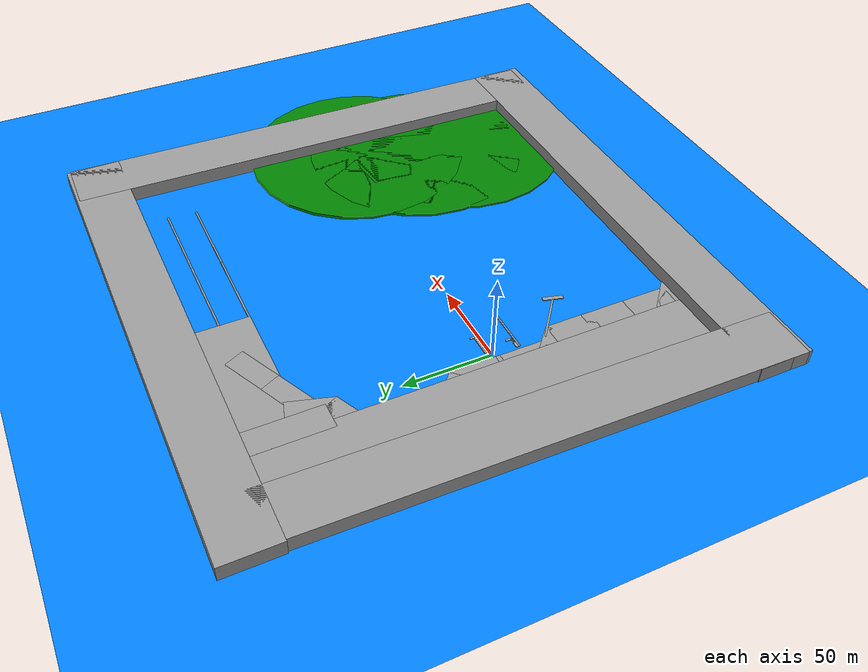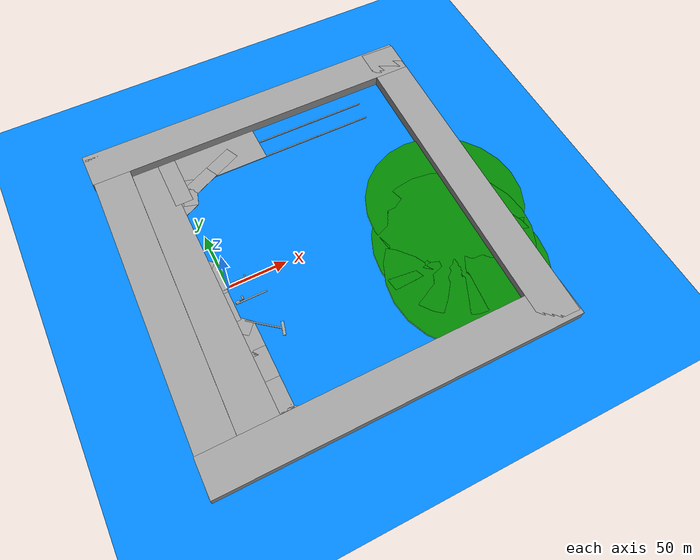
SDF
<sdf version="1.7">
 <world name="default">
  <light name="sun" type="directional">
   <pose>0 0 10 0 -0 0</pose>
   <diffuse>0.8 0.8 0.8 1</diffuse>
   <specular>0.2 0.2 0.2 1</specular>
   <attenuation>
    <range>1000</range>
    <constant>0.9</constant>
    <linear>0.01</linear>
    <quadratic>0.001</quadratic>
   </attenuation>
   <direction>-0.5 0.1 -0.9</direction>
   <spot><inner_angle>0</inner_angle><outer_angle>0</outer_angle><falloff>0</falloff></spot>
  </light>
  <model name="ground_plane">
   <static>1</static>
   <link name="link">
    <collision name="collision">
     <geometry><plane><normal>0 0 1</normal><size>1000 1000</size></plane></geometry>
     <surface><friction><ode><mu>100</mu><mu2>50</mu2></ode></friction></surface>
    </collision>
    <visual name="visual">
     <cast_shadows>0</cast_shadows>
     <geometry><plane><normal>0 0 1</normal><size>1000 1000</size></plane></geometry>
     <material>
      <ambient>0 0.5 1 1</ambient>
      <diffuse>0 0.5 1 1</diffuse>
      <specular>0.1 0.1 0.1 1</specular>
      <emissive>0 0 0 0</emissive>
     </material>
    </visual>
   </link>
  </model>
  <gravity>0 0 -9.8</gravity>
  <magnetic_field>6e-06 2.3e-05 -4.2e-05</magnetic_field>
  <atmosphere type="adiabatic"/>
  <physics type="ode">
   <max_step_size>0.001</max_step_size>
   <real_time_factor>1</real_time_factor>
   <real_time_update_rate>1000</real_time_update_rate>
  </physics>
  <scene><ambient>0.4 0.4 0.4 1</ambient><background>0.7 0.7 0.7 1</background><shadows>1</shadows></scene>
  <audio><device>default</device></audio>
  <spherical_coordinates>
   <surface_model>EARTH_WGS84</surface_model>
   <latitude_deg>0</latitude_deg>
   <longitude_deg>0</longitude_deg>
   <elevation>0</elevation>
   <heading_deg>0</heading_deg>
  </spherical_coordinates>
  <model name="ground">
   <link name="link">
    <inertial>
     <mass>1</mass>
     <inertia>
      <ixx>0.166667</ixx>
      <ixy>0</ixy>
      <ixz>0</ixz>
      <iyy>0.166667</iyy>
      <iyz>0</iyz>
      <izz>0.166667</izz>
     </inertia>
    </inertial>
    <pose>0 2.71082 0 0 -0 0</pose>
    <visual name="visual">
     <geometry><box><size>12.2775 26.0732 0.428308</size></box></geometry>
     <material>
      <lighting>1</lighting>
      <script><uri>file://media/materials/scripts/gazebo.material</uri><name>Gazebo/Grey</name></script>
      <shader type="pixel"/>
     </material>
    </visual>
    <collision name="collision">
     <geometry><box><size>12.2775 26.0732 0.428308</size></box></geometry>
     <surface>
      <friction>
       <ode><mu>1</mu><mu2>1</mu2><fdir1>0 0 0</fdir1><slip1>0</slip1><slip2>0</slip2></ode>
       <torsional>
        <coefficient>1</coefficient>
        <patch_radius>0</patch_radius>
        <surface_radius>0</surface_radius>
        <use_patch_radius>1</use_patch_radius>
        <ode><slip>0</slip></ode>
       </torsional>
      </friction>
      <bounce><restitution_coefficient>0</restitution_coefficient><threshold>1e+06</threshold></bounce>
      <contact>
       <collide_without_contact>0</collide_without_contact>
       <collide_without_contact_bitmask>1</collide_without_contact_bitmask>
       <collide_bitmask>1</collide_bitmask>
       <ode>
        <soft_cfm>0</soft_cfm>
        <soft_erp>0.2</soft_erp>
        <kp>1e+13</kp>
        <kd>1</kd>
        <max_vel>0.01</max_vel>
        <min_depth>0</min_depth>
       </ode>
       <bullet>
        <split_impulse>1</split_impulse>
        <split_impulse_penetration_threshold>-0.01</split_impulse_penetration_threshold>
        <soft_cfm>0</soft_cfm>
        <soft_erp>0.2</soft_erp>
        <kp>1e+13</kp>
        <kd>1</kd>
       </bullet>
      </contact>
     </surface>
    </collision>
   </link>
   <link name="link_clone">
    <inertial>
     <mass>1</mass>
     <inertia>
      <ixx>0.166667</ixx>
      <ixy>0</ixy>
      <ixz>0</ixz>
      <iyy>0.166667</iyy>
      <iyz>0</iyz>
      <izz>0.166667</izz>
     </inertia>
    </inertial>
    <pose>-7.60672 19.8582 0 0 -0 0.838579</pose>
    <visual name="visual">
     <geometry><box><size>12.2775 26.0732 0.428308</size></box></geometry>
     <material>
      <lighting>1</lighting>
      <script><uri>file://media/materials/scripts/gazebo.material</uri><name>Gazebo/Grey</name></script>
      <shader type="pixel"/>
     </material>
    </visual>
    <collision name="collision">
     <geometry><box><size>12.2775 26.0732 0.428308</size></box></geometry>
     <surface>
      <friction>
       <ode><mu>1</mu><mu2>1</mu2><fdir1>0 0 0</fdir1><slip1>0</slip1><slip2>0</slip2></ode>
       <torsional>
        <coefficient>1</coefficient>
        <patch_radius>0</patch_radius>
        <surface_radius>0</surface_radius>
        <use_patch_radius>1</use_patch_radius>
        <ode><slip>0</slip></ode>
       </torsional>
      </friction>
      <bounce><restitution_coefficient>0</restitution_coefficient><threshold>1e+06</threshold></bounce>
      <contact>
       <collide_without_contact>0</collide_without_contact>
       <collide_without_contact_bitmask>1</collide_without_contact_bitmask>
       <collide_bitmask>1</collide_bitmask>
       <ode>
        <soft_cfm>0</soft_cfm>
        <soft_erp>0.2</soft_erp>
        <kp>1e+13</kp>
        <kd>1</kd>
        <max_vel>0.01</max_vel>
        <min_depth>0</min_depth>
       </ode>
       <bullet>
        <split_impulse>1</split_impulse>
        <split_impulse_penetration_threshold>-0.01</split_impulse_penetration_threshold>
        <soft_cfm>0</soft_cfm>
        <soft_erp>0.2</soft_erp>
        <kp>1e+13</kp>
        <kd>1</kd>
       </bullet>
      </contact>
     </surface>
    </collision>
   </link>
   <link name="link_clone_0">
    <inertial>
     <mass>1</mass>
     <inertia>
      <ixx>0.166667</ixx>
      <ixy>0</ixy>
      <ixz>0</ixz>
      <iyy>0.166667</iyy>
      <iyz>0</iyz>
      <izz>0.166667</izz>
     </inertia>
    </inertial>
    <pose>-8.13936 34.3499 0 0 -0 0</pose>
    <visual name="visual">
     <geometry><box><size>12.2775 26.0732 0.428308</size></box></geometry>
     <material>
      <lighting>1</lighting>
      <script><uri>file://media/materials/scripts/gazebo.material</uri><name>Gazebo/Grey</name></script>
      <shader type="pixel"/>
     </material>
    </visual>
    <collision name="collision">
     <geometry><box><size>12.2775 26.0732 0.428308</size></box></geometry>
     <surface>
      <friction>
       <ode><mu>1</mu><mu2>1</mu2><fdir1>0 0 0</fdir1><slip1>0</slip1><slip2>0</slip2></ode>
       <torsional>
        <coefficient>1</coefficient>
        <patch_radius>0</patch_radius>
        <surface_radius>0</surface_radius>
        <use_patch_radius>1</use_patch_radius>
        <ode><slip>0</slip></ode>
       </torsional>
      </friction>
      <bounce><restitution_coefficient>0</restitution_coefficient><threshold>1e+06</threshold></bounce>
      <contact>
       <collide_without_contact>0</collide_without_contact>
       <collide_without_contact_bitmask>1</collide_without_contact_bitmask>
       <collide_bitmask>1</collide_bitmask>
       <ode>
        <soft_cfm>0</soft_cfm>
        <soft_erp>0.2</soft_erp>
        <kp>1e+13</kp>
        <kd>1</kd>
        <max_vel>0.01</max_vel>
        <min_depth>0</min_depth>
       </ode>
       <bullet>
        <split_impulse>1</split_impulse>
        <split_impulse_penetration_threshold>-0.01</split_impulse_penetration_threshold>
        <soft_cfm>0</soft_cfm>
        <soft_erp>0.2</soft_erp>
        <kp>1e+13</kp>
        <kd>1</kd>
       </bullet>
      </contact>
     </surface>
    </collision>
   </link>
   <link name="link_clone_0_clone">
    <inertial>
     <mass>1</mass>
     <inertia>
      <ixx>0.166667</ixx>
      <ixy>0</ixy>
      <ixz>0</ixz>
      <iyy>0.166667</iyy>
      <iyz>0</iyz>
      <izz>0.166667</izz>
     </inertia>
    </inertial>
    <pose>-8.03787 60.3254 0 0 -0 0</pose>
    <visual name="visual">
     <geometry><box><size>12.2775 26.0732 0.428308</size></box></geometry>
     <material>
      <lighting>1</lighting>
      <script><uri>file://media/materials/scripts/gazebo.material</uri><name>Gazebo/Grey</name></script>
      <shader type="pixel"/>
     </material>
    </visual>
    <collision name="collision">
     <geometry><box><size>12.2775 26.0732 0.428308</size></box></geometry>
     <surface>
      <friction>
       <ode><mu>1</mu><mu2>1</mu2><fdir1>0 0 0</fdir1><slip1>0</slip1><slip2>0</slip2></ode>
       <torsional>
        <coefficient>1</coefficient>
        <patch_radius>0</patch_radius>
        <surface_radius>0</surface_radius>
        <use_patch_radius>1</use_patch_radius>
        <ode><slip>0</slip></ode>
       </torsional>
      </friction>
      <bounce><restitution_coefficient>0</restitution_coefficient><threshold>1e+06</threshold></bounce>
      <contact>
       <collide_without_contact>0</collide_without_contact>
       <collide_without_contact_bitmask>1</collide_without_contact_bitmask>
       <collide_bitmask>1</collide_bitmask>
       <ode>
        <soft_cfm>0</soft_cfm>
        <soft_erp>0.2</soft_erp>
        <kp>1e+13</kp>
        <kd>1</kd>
        <max_vel>0.01</max_vel>
        <min_depth>0</min_depth>
       </ode>
       <bullet>
        <split_impulse>1</split_impulse>
        <split_impulse_penetration_threshold>-0.01</split_impulse_penetration_threshold>
        <soft_cfm>0</soft_cfm>
        <soft_erp>0.2</soft_erp>
        <kp>1e+13</kp>
        <kd>1</kd>
       </bullet>
      </contact>
     </surface>
    </collision>
   </link>
   <static>1</static>
   <pose>0.250638 -51.022 0.106728 0 -0 0</pose>
  </model>
  <model name="ground_clone">
   <link name="link">
    <inertial>
     <mass>1</mass>
     <inertia>
      <ixx>0.166667</ixx>
      <ixy>0</ixy>
      <ixz>0</ixz>
      <iyy>0.166667</iyy>
      <iyz>0</iyz>
      <izz>0.166667</izz>
     </inertia>
    </inertial>
    <pose>0 2.71082 0 0 -0 0</pose>
    <visual name="visual">
     <geometry><box><size>12.2775 26.0732 0.428308</size></box></geometry>
     <material>
      <lighting>1</lighting>
      <script><uri>file://media/materials/scripts/gazebo.material</uri><name>Gazebo/Grey</name></script>
      <shader type="pixel"/>
     </material>
    </visual>
    <collision name="collision">
     <geometry><box><size>12.2775 26.0732 0.428308</size></box></geometry>
     <surface>
      <friction>
       <ode><mu>1</mu><mu2>1</mu2><fdir1>0 0 0</fdir1><slip1>0</slip1><slip2>0</slip2></ode>
       <torsional>
        <coefficient>1</coefficient>
        <patch_radius>0</patch_radius>
        <surface_radius>0</surface_radius>
        <use_patch_radius>1</use_patch_radius>
        <ode><slip>0</slip></ode>
       </torsional>
      </friction>
      <bounce><restitution_coefficient>0</restitution_coefficient><threshold>1e+06</threshold></bounce>
      <contact>
       <collide_without_contact>0</collide_without_contact>
       <collide_without_contact_bitmask>1</collide_without_contact_bitmask>
       <collide_bitmask>1</collide_bitmask>
       <ode>
        <soft_cfm>0</soft_cfm>
        <soft_erp>0.2</soft_erp>
        <kp>1e+13</kp>
        <kd>1</kd>
        <max_vel>0.01</max_vel>
        <min_depth>0</min_depth>
       </ode>
       <bullet>
        <split_impulse>1</split_impulse>
        <split_impulse_penetration_threshold>-0.01</split_impulse_penetration_threshold>
        <soft_cfm>0</soft_cfm>
        <soft_erp>0.2</soft_erp>
        <kp>1e+13</kp>
        <kd>1</kd>
       </bullet>
      </contact>
     </surface>
    </collision>
   </link>
   <link name="link_clone">
    <inertial>
     <mass>1</mass>
     <inertia>
      <ixx>0.166667</ixx>
      <ixy>0</ixy>
      <ixz>0</ixz>
      <iyy>0.166667</iyy>
      <iyz>0</iyz>
      <izz>0.166667</izz>
     </inertia>
    </inertial>
    <pose>-7.60672 19.8582 0 0 -0 0.838579</pose>
    <visual name="visual">
     <geometry><box><size>12.2775 26.0732 0.428308</size></box></geometry>
     <material>
      <lighting>1</lighting>
      <script><uri>file://media/materials/scripts/gazebo.material</uri><name>Gazebo/Grey</name></script>
      <shader type="pixel"/>
     </material>
    </visual>
    <collision name="collision">
     <geometry><box><size>12.2775 26.0732 0.428308</size></box></geometry>
     <surface>
      <friction>
       <ode><mu>1</mu><mu2>1</mu2><fdir1>0 0 0</fdir1><slip1>0</slip1><slip2>0</slip2></ode>
       <torsional>
        <coefficient>1</coefficient>
        <patch_radius>0</patch_radius>
        <surface_radius>0</surface_radius>
        <use_patch_radius>1</use_patch_radius>
        <ode><slip>0</slip></ode>
       </torsional>
      </friction>
      <bounce><restitution_coefficient>0</restitution_coefficient><threshold>1e+06</threshold></bounce>
      <contact>
       <collide_without_contact>0</collide_without_contact>
       <collide_without_contact_bitmask>1</collide_without_contact_bitmask>
       <collide_bitmask>1</collide_bitmask>
       <ode>
        <soft_cfm>0</soft_cfm>
        <soft_erp>0.2</soft_erp>
        <kp>1e+13</kp>
        <kd>1</kd>
        <max_vel>0.01</max_vel>
        <min_depth>0</min_depth>
       </ode>
       <bullet>
        <split_impulse>1</split_impulse>
        <split_impulse_penetration_threshold>-0.01</split_impulse_penetration_threshold>
        <soft_cfm>0</soft_cfm>
        <soft_erp>0.2</soft_erp>
        <kp>1e+13</kp>
        <kd>1</kd>
       </bullet>
      </contact>
     </surface>
    </collision>
   </link>
   <link name="link_clone_0">
    <inertial>
     <mass>1</mass>
     <inertia>
      <ixx>0.166667</ixx>
      <ixy>0</ixy>
      <ixz>0</ixz>
      <iyy>0.166667</iyy>
      <iyz>0</iyz>
      <izz>0.166667</izz>
     </inertia>
    </inertial>
    <pose>-8.13936 34.3499 0 0 -0 0</pose>
    <visual name="visual">
     <geometry><box><size>12.2775 26.0732 0.428308</size></box></geometry>
     <material>
      <lighting>1</lighting>
      <script><uri>file://media/materials/scripts/gazebo.material</uri><name>Gazebo/Grey</name></script>
      <shader type="pixel"/>
     </material>
    </visual>
    <collision name="collision">
     <geometry><box><size>12.2775 26.0732 0.428308</size></box></geometry>
     <surface>
      <friction>
       <ode><mu>1</mu><mu2>1</mu2><fdir1>0 0 0</fdir1><slip1>0</slip1><slip2>0</slip2></ode>
       <torsional>
        <coefficient>1</coefficient>
        <patch_radius>0</patch_radius>
        <surface_radius>0</surface_radius>
        <use_patch_radius>1</use_patch_radius>
        <ode><slip>0</slip></ode>
       </torsional>
      </friction>
      <bounce><restitution_coefficient>0</restitution_coefficient><threshold>1e+06</threshold></bounce>
      <contact>
       <collide_without_contact>0</collide_without_contact>
       <collide_without_contact_bitmask>1</collide_without_contact_bitmask>
       <collide_bitmask>1</collide_bitmask>
       <ode>
        <soft_cfm>0</soft_cfm>
        <soft_erp>0.2</soft_erp>
        <kp>1e+13</kp>
        <kd>1</kd>
        <max_vel>0.01</max_vel>
        <min_depth>0</min_depth>
       </ode>
       <bullet>
        <split_impulse>1</split_impulse>
        <split_impulse_penetration_threshold>-0.01</split_impulse_penetration_threshold>
        <soft_cfm>0</soft_cfm>
        <soft_erp>0.2</soft_erp>
        <kp>1e+13</kp>
        <kd>1</kd>
       </bullet>
      </contact>
     </surface>
    </collision>
   </link>
   <link name="link_clone_0_clone">
    <inertial>
     <mass>1</mass>
     <inertia>
      <ixx>0.166667</ixx>
      <ixy>0</ixy>
      <ixz>0</ixz>
      <iyy>0.166667</iyy>
      <iyz>0</iyz>
      <izz>0.166667</izz>
     </inertia>
    </inertial>
    <pose>-8.03787 60.3254 0 0 -0 0</pose>
    <visual name="visual">
     <geometry><box><size>12.2775 26.0732 0.428308</size></box></geometry>
     <material>
      <lighting>1</lighting>
      <script><uri>file://media/materials/scripts/gazebo.material</uri><name>Gazebo/Grey</name></script>
      <shader type="pixel"/>
     </material>
    </visual>
    <collision name="collision">
     <geometry><box><size>12.2775 26.0732 0.428308</size></box></geometry>
     <surface>
      <friction>
       <ode><mu>1</mu><mu2>1</mu2><fdir1>0 0 0</fdir1><slip1>0</slip1><slip2>0</slip2></ode>
       <torsional>
        <coefficient>1</coefficient>
        <patch_radius>0</patch_radius>
        <surface_radius>0</surface_radius>
        <use_patch_radius>1</use_patch_radius>
        <ode><slip>0</slip></ode>
       </torsional>
      </friction>
      <bounce><restitution_coefficient>0</restitution_coefficient><threshold>1e+06</threshold></bounce>
      <contact>
       <collide_without_contact>0</collide_without_contact>
       <collide_without_contact_bitmask>1</collide_without_contact_bitmask>
       <collide_bitmask>1</collide_bitmask>
       <ode>
        <soft_cfm>0</soft_cfm>
        <soft_erp>0.2</soft_erp>
        <kp>1e+13</kp>
        <kd>1</kd>
        <max_vel>0.01</max_vel>
        <min_depth>0</min_depth>
       </ode>
       <bullet>
        <split_impulse>1</split_impulse>
        <split_impulse_penetration_threshold>-0.01</split_impulse_penetration_threshold>
        <soft_cfm>0</soft_cfm>
        <soft_erp>0.2</soft_erp>
        <kp>1e+13</kp>
        <kd>1</kd>
       </bullet>
      </contact>
     </surface>
    </collision>
   </link>
   <static>1</static>
   <pose>-7.76388 9.13868 0.121126 0 -0 0</pose>
  </model>
  <model name="ground_clone_0">
   <link name="link">
    <inertial>
     <mass>1</mass>
     <inertia>
      <ixx>0.166667</ixx>
      <ixy>0</ixy>
      <ixz>0</ixz>
      <iyy>0.166667</iyy>
      <iyz>0</iyz>
      <izz>0.166667</izz>
     </inertia>
    </inertial>
    <pose>0 2.71082 0 0 -0 0</pose>
    <visual name="visual">
     <geometry><box><size>12.2775 26.0732 0.428308</size></box></geometry>
     <material>
      <lighting>1</lighting>
      <script><uri>file://media/materials/scripts/gazebo.material</uri><name>Gazebo/Grey</name></script>
      <shader type="pixel"/>
     </material>
    </visual>
    <collision name="collision">
     <geometry><box><size>12.2775 26.0732 0.428308</size></box></geometry>
     <surface>
      <friction>
       <ode><mu>1</mu><mu2>1</mu2><fdir1>0 0 0</fdir1><slip1>0</slip1><slip2>0</slip2></ode>
       <torsional>
        <coefficient>1</coefficient>
        <patch_radius>0</patch_radius>
        <surface_radius>0</surface_radius>
        <use_patch_radius>1</use_patch_radius>
        <ode><slip>0</slip></ode>
       </torsional>
      </friction>
      <bounce><restitution_coefficient>0</restitution_coefficient><threshold>1e+06</threshold></bounce>
      <contact>
       <collide_without_contact>0</collide_without_contact>
       <collide_without_contact_bitmask>1</collide_without_contact_bitmask>
       <collide_bitmask>1</collide_bitmask>
       <ode>
        <soft_cfm>0</soft_cfm>
        <soft_erp>0.2</soft_erp>
        <kp>1e+13</kp>
        <kd>1</kd>
        <max_vel>0.01</max_vel>
        <min_depth>0</min_depth>
       </ode>
       <bullet>
        <split_impulse>1</split_impulse>
        <split_impulse_penetration_threshold>-0.01</split_impulse_penetration_threshold>
        <soft_cfm>0</soft_cfm>
        <soft_erp>0.2</soft_erp>
        <kp>1e+13</kp>
        <kd>1</kd>
       </bullet>
      </contact>
     </surface>
    </collision>
   </link>
   <link name="link_clone">
    <inertial>
     <mass>1</mass>
     <inertia>
      <ixx>0.166667</ixx>
      <ixy>0</ixy>
      <ixz>0</ixz>
      <iyy>0.166667</iyy>
      <iyz>0</iyz>
      <izz>0.166667</izz>
     </inertia>
    </inertial>
    <pose>-7.60672 19.8582 0 0 -0 0.838579</pose>
    <visual name="visual">
     <geometry><box><size>12.2775 26.0732 0.428308</size></box></geometry>
     <material>
      <lighting>1</lighting>
      <script><uri>file://media/materials/scripts/gazebo.material</uri><name>Gazebo/Grey</name></script>
      <shader type="pixel"/>
     </material>
    </visual>
    <collision name="collision">
     <geometry><box><size>12.2775 26.0732 0.428308</size></box></geometry>
     <surface>
      <friction>
       <ode><mu>1</mu><mu2>1</mu2><fdir1>0 0 0</fdir1><slip1>0</slip1><slip2>0</slip2></ode>
       <torsional>
        <coefficient>1</coefficient>
        <patch_radius>0</patch_radius>
        <surface_radius>0</surface_radius>
        <use_patch_radius>1</use_patch_radius>
        <ode><slip>0</slip></ode>
       </torsional>
      </friction>
      <bounce><restitution_coefficient>0</restitution_coefficient><threshold>1e+06</threshold></bounce>
      <contact>
       <collide_without_contact>0</collide_without_contact>
       <collide_without_contact_bitmask>1</collide_without_contact_bitmask>
       <collide_bitmask>1</collide_bitmask>
       <ode>
        <soft_cfm>0</soft_cfm>
        <soft_erp>0.2</soft_erp>
        <kp>1e+13</kp>
        <kd>1</kd>
        <max_vel>0.01</max_vel>
        <min_depth>0</min_depth>
       </ode>
       <bullet>
        <split_impulse>1</split_impulse>
        <split_impulse_penetration_threshold>-0.01</split_impulse_penetration_threshold>
        <soft_cfm>0</soft_cfm>
        <soft_erp>0.2</soft_erp>
        <kp>1e+13</kp>
        <kd>1</kd>
       </bullet>
      </contact>
     </surface>
    </collision>
   </link>
   <link name="link_clone_0">
    <inertial>
     <mass>1</mass>
     <inertia>
      <ixx>0.166667</ixx>
      <ixy>0</ixy>
      <ixz>0</ixz>
      <iyy>0.166667</iyy>
      <iyz>0</iyz>
      <izz>0.166667</izz>
     </inertia>
    </inertial>
    <pose>-8.13936 34.3499 0 0 -0 0</pose>
    <visual name="visual">
     <geometry><box><size>12.2775 26.0732 0.428308</size></box></geometry>
     <material>
      <lighting>1</lighting>
      <script><uri>file://media/materials/scripts/gazebo.material</uri><name>Gazebo/Grey</name></script>
      <shader type="pixel"/>
     </material>
    </visual>
    <collision name="collision">
     <geometry><box><size>12.2775 26.0732 0.428308</size></box></geometry>
     <surface>
      <friction>
       <ode><mu>1</mu><mu2>1</mu2><fdir1>0 0 0</fdir1><slip1>0</slip1><slip2>0</slip2></ode>
       <torsional>
        <coefficient>1</coefficient>
        <patch_radius>0</patch_radius>
        <surface_radius>0</surface_radius>
        <use_patch_radius>1</use_patch_radius>
        <ode><slip>0</slip></ode>
       </torsional>
      </friction>
      <bounce><restitution_coefficient>0</restitution_coefficient><threshold>1e+06</threshold></bounce>
      <contact>
       <collide_without_contact>0</collide_without_contact>
       <collide_without_contact_bitmask>1</collide_without_contact_bitmask>
       <collide_bitmask>1</collide_bitmask>
       <ode>
        <soft_cfm>0</soft_cfm>
        <soft_erp>0.2</soft_erp>
        <kp>1e+13</kp>
        <kd>1</kd>
        <max_vel>0.01</max_vel>
        <min_depth>0</min_depth>
       </ode>
       <bullet>
        <split_impulse>1</split_impulse>
        <split_impulse_penetration_threshold>-0.01</split_impulse_penetration_threshold>
        <soft_cfm>0</soft_cfm>
        <soft_erp>0.2</soft_erp>
        <kp>1e+13</kp>
        <kd>1</kd>
       </bullet>
      </contact>
     </surface>
    </collision>
   </link>
   <link name="link_clone_0_clone">
    <inertial>
     <mass>1</mass>
     <inertia>
      <ixx>0.166667</ixx>
      <ixy>0</ixy>
      <ixz>0</ixz>
      <iyy>0.166667</iyy>
      <iyz>0</iyz>
      <izz>0.166667</izz>
     </inertia>
    </inertial>
    <pose>-8.03787 60.3254 0 0 -0 0</pose>
    <visual name="visual">
     <geometry><box><size>12.2775 26.0732 0.428308</size></box></geometry>
     <material>
      <lighting>1</lighting>
      <script><uri>file://media/materials/scripts/gazebo.material</uri><name>Gazebo/Grey</name></script>
      <shader type="pixel"/>
     </material>
    </visual>
    <collision name="collision">
     <geometry><box><size>12.2775 26.0732 0.428308</size></box></geometry>
     <surface>
      <friction>
       <ode><mu>1</mu><mu2>1</mu2><fdir1>0 0 0</fdir1><slip1>0</slip1><slip2>0</slip2></ode>
       <torsional>
        <coefficient>1</coefficient>
        <patch_radius>0</patch_radius>
        <surface_radius>0</surface_radius>
        <use_patch_radius>1</use_patch_radius>
        <ode><slip>0</slip></ode>
       </torsional>
      </friction>
      <bounce><restitution_coefficient>0</restitution_coefficient><threshold>1e+06</threshold></bounce>
      <contact>
       <collide_without_contact>0</collide_without_contact>
       <collide_without_contact_bitmask>1</collide_without_contact_bitmask>
       <collide_bitmask>1</collide_bitmask>
       <ode>
        <soft_cfm>0</soft_cfm>
        <soft_erp>0.2</soft_erp>
        <kp>1e+13</kp>
        <kd>1</kd>
        <max_vel>0.01</max_vel>
        <min_depth>0</min_depth>
       </ode>
       <bullet>
        <split_impulse>1</split_impulse>
        <split_impulse_penetration_threshold>-0.01</split_impulse_penetration_threshold>
        <soft_cfm>0</soft_cfm>
        <soft_erp>0.2</soft_erp>
        <kp>1e+13</kp>
        <kd>1</kd>
       </bullet>
      </contact>
     </surface>
    </collision>
   </link>
   <static>1</static>
   <pose>-9.88185 80.6091 0.120152 0 0 -1.12831</pose>
  </model>
  <model name="Untitled"><pose>61.4045 -75.8074 0 0 -0 0</pose><static>1</static></model>
  <model name="pontoon1">
   <link name="link">
    <inertial>
     <mass>6.89723</mass>
     <inertia><ixx>0.699771</ixx><ixy>0</ixy><ixz>0</ixz><iyy>125.749</iyy><iyz>0</iyz><izz>126.198</izz></inertia>
    </inertial>
    <pose>6.89493 0 -0.43683 0 -0 0</pose>
    <visual name="visual">
     <geometry><box><size>14.7839 1 0.466349</size></box></geometry>
     <material>
      <script><name>Gazebo/Grey</name><uri>file://media/materials/scripts/gazebo.material</uri></script>
      <shader type="pixel"/>
     </material>
    </visual>
    <collision name="collision">
     <geometry><box><size>14.7839 1 0.466349</size></box></geometry>
     <surface>
      <friction>
       <ode><mu>1</mu><mu2>1</mu2><fdir1>0 0 0</fdir1><slip1>0</slip1><slip2>0</slip2></ode>
       <torsional>
        <coefficient>1</coefficient>
        <patch_radius>0</patch_radius>
        <surface_radius>0</surface_radius>
        <use_patch_radius>1</use_patch_radius>
        <ode><slip>0</slip></ode>
       </torsional>
      </friction>
      <bounce><restitution_coefficient>0</restitution_coefficient><threshold>1e+06</threshold></bounce>
      <contact>
       <collide_without_contact>0</collide_without_contact>
       <collide_without_contact_bitmask>1</collide_without_contact_bitmask>
       <collide_bitmask>1</collide_bitmask>
       <ode>
        <soft_cfm>0</soft_cfm>
        <soft_erp>0.2</soft_erp>
        <kp>1e+13</kp>
        <kd>1</kd>
        <max_vel>0.01</max_vel>
        <min_depth>0</min_depth>
       </ode>
       <bullet>
        <split_impulse>1</split_impulse>
        <split_impulse_penetration_threshold>-0.01</split_impulse_penetration_threshold>
        <soft_cfm>0</soft_cfm>
        <soft_erp>0.2</soft_erp>
        <kp>1e+13</kp>
        <kd>1</kd>
       </bullet>
      </contact>
     </surface>
    </collision>
   </link>
   <link name="link_0">
    <inertial>
     <mass>2.18615</mass>
     <inertia><ixx>5.06693</ixx><ixy>0</ixy><ixz>0</ixz><iyy>0.213678</iyy><iyz>0</iyz><izz>5.21761</izz></inertia>
    </inertial>
    <pose>14.7716 0.008705 -0.420134 0 -0 0</pose>
    <visual name="visual">
     <geometry><box><size>1 5.25737 0.415813</size></box></geometry>
     <material>
      <script><name>Gazebo/Grey</name><uri>file://media/materials/scripts/gazebo.material</uri></script>
      <shader type="pixel"/>
     </material>
    </visual>
    <collision name="collision">
     <geometry><box><size>1 5.25737 0.415813</size></box></geometry>
     <surface>
      <friction>
       <ode><mu>1</mu><mu2>1</mu2><fdir1>0 0 0</fdir1><slip1>0</slip1><slip2>0</slip2></ode>
       <torsional>
        <coefficient>1</coefficient>
        <patch_radius>0</patch_radius>
        <surface_radius>0</surface_radius>
        <use_patch_radius>1</use_patch_radius>
        <ode><slip>0</slip></ode>
       </torsional>
      </friction>
      <bounce><restitution_coefficient>0</restitution_coefficient><threshold>1e+06</threshold></bounce>
      <contact>
       <collide_without_contact>0</collide_without_contact>
       <collide_without_contact_bitmask>1</collide_without_contact_bitmask>
       <collide_bitmask>1</collide_bitmask>
       <ode>
        <soft_cfm>0</soft_cfm>
        <soft_erp>0.2</soft_erp>
        <kp>1e+13</kp>
        <kd>1</kd>
        <max_vel>0.01</max_vel>
        <min_depth>0</min_depth>
       </ode>
       <bullet>
        <split_impulse>1</split_impulse>
        <split_impulse_penetration_threshold>-0.01</split_impulse_penetration_threshold>
        <soft_cfm>0</soft_cfm>
        <soft_erp>0.2</soft_erp>
        <kp>1e+13</kp>
        <kd>1</kd>
       </bullet>
      </contact>
     </surface>
    </collision>
   </link>
   <static>1</static>
   <pose>0.43633 1.97194 0.5 0 -0 0</pose>
  </model>
  <model name="pontoon2">
   <link name="link">
    <inertial>
     <mass>2.03797</mass>
     <inertia><ixx>0.198693</ixx><ixy>0</ixy><ixz>0</ixz><iyy>112.631</iyy><iyz>0</iyz><izz>112.772</izz></inertia>
    </inertial>
    <visual name="visual">
     <geometry><box><size>25.7492 1 0.412244</size></box></geometry>
     <material>
      <script><name>Gazebo/Grey</name><uri>file://media/materials/scripts/gazebo.material</uri></script>
      <shader type="pixel"/>
     </material>
    </visual>
    <collision name="collision">
     <geometry><box><size>25.7492 1 0.412244</size></box></geometry>
     <surface>
      <friction>
       <ode><mu>1</mu><mu2>1</mu2><fdir1>0 0 0</fdir1><slip1>0</slip1><slip2>0</slip2></ode>
       <torsional>
        <coefficient>1</coefficient>
        <patch_radius>0</patch_radius>
        <surface_radius>0</surface_radius>
        <use_patch_radius>1</use_patch_radius>
        <ode><slip>0</slip></ode>
       </torsional>
      </friction>
      <bounce><restitution_coefficient>0</restitution_coefficient><threshold>1e+06</threshold></bounce>
      <contact>
       <collide_without_contact>0</collide_without_contact>
       <collide_without_contact_bitmask>1</collide_without_contact_bitmask>
       <collide_bitmask>1</collide_bitmask>
       <ode>
        <soft_cfm>0</soft_cfm>
        <soft_erp>0.2</soft_erp>
        <kp>1e+13</kp>
        <kd>1</kd>
        <max_vel>0.01</max_vel>
        <min_depth>0</min_depth>
       </ode>
       <bullet>
        <split_impulse>1</split_impulse>
        <split_impulse_penetration_threshold>-0.01</split_impulse_penetration_threshold>
        <soft_cfm>0</soft_cfm>
        <soft_erp>0.2</soft_erp>
        <kp>1e+13</kp>
        <kd>1</kd>
       </bullet>
      </contact>
     </surface>
    </collision>
   </link>
   <link name="link_clone">
    <inertial>
     <mass>0.0692908</mass>
     <inertia>
      <ixx>0.00119337</ixx>
      <ixy>0</ixy>
      <ixz>0</ixz>
      <iyy>0.0726039</iyy>
      <iyz>0</iyz>
      <izz>0.072785</izz>
     </inertia>
    </inertial>
    <pose>-7.77701 1.36068 0 0 -0 0</pose>
    <visual name="visual">
     <geometry><box><size>3.53357 0.344994 0.296059</size></box></geometry>
     <material>
      <script><name>Gazebo/Grey</name><uri>file://media/materials/scripts/gazebo.material</uri></script>
      <shader type="pixel"/>
     </material>
    </visual>
    <collision name="collision">
     <geometry><box><size>3.53357 0.344994 0.296059</size></box></geometry>
     <surface>
      <friction>
       <ode><mu>1</mu><mu2>1</mu2><fdir1>0 0 0</fdir1><slip1>0</slip1><slip2>0</slip2></ode>
       <torsional>
        <coefficient>1</coefficient>
        <patch_radius>0</patch_radius>
        <surface_radius>0</surface_radius>
        <use_patch_radius>1</use_patch_radius>
        <ode><slip>0</slip></ode>
       </torsional>
      </friction>
      <bounce><restitution_coefficient>0</restitution_coefficient><threshold>1e+06</threshold></bounce>
      <contact>
       <collide_without_contact>0</collide_without_contact>
       <collide_without_contact_bitmask>1</collide_without_contact_bitmask>
       <collide_bitmask>1</collide_bitmask>
       <ode>
        <soft_cfm>0</soft_cfm>
        <soft_erp>0.2</soft_erp>
        <kp>1e+13</kp>
        <kd>1</kd>
        <max_vel>0.01</max_vel>
        <min_depth>0</min_depth>
       </ode>
       <bullet>
        <split_impulse>1</split_impulse>
        <split_impulse_penetration_threshold>-0.01</split_impulse_penetration_threshold>
        <soft_cfm>0</soft_cfm>
        <soft_erp>0.2</soft_erp>
        <kp>1e+13</kp>
        <kd>1</kd>
       </bullet>
      </contact>
     </surface>
    </collision>
   </link>
   <link name="link_clone_clone">
    <inertial>
     <mass>0.498797</mass>
     <inertia>
      <ixx>0.172417</ixx>
      <ixy>0</ixy>
      <ixz>0</ixz>
      <iyy>0.524602</iyy>
      <iyz>0</iyz>
      <izz>0.685821</izz>
     </inertia>
    </inertial>
    <pose>-11.19 1.03862 0 0 -0 0</pose>
    <visual name="visual">
     <geometry><box><size>3.53357 2.00332 0.367019</size></box></geometry>
     <material>
      <script><name>Gazebo/Grey</name><uri>file://media/materials/scripts/gazebo.material</uri></script>
      <shader type="pixel"/>
     </material>
    </visual>
    <collision name="collision">
     <geometry><box><size>3.53357 2.00332 0.367019</size></box></geometry>
     <surface>
      <friction>
       <ode><mu>1</mu><mu2>1</mu2><fdir1>0 0 0</fdir1><slip1>0</slip1><slip2>0</slip2></ode>
       <torsional>
        <coefficient>1</coefficient>
        <patch_radius>0</patch_radius>
        <surface_radius>0</surface_radius>
        <use_patch_radius>1</use_patch_radius>
        <ode><slip>0</slip></ode>
       </torsional>
      </friction>
      <bounce><restitution_coefficient>0</restitution_coefficient><threshold>1e+06</threshold></bounce>
      <contact>
       <collide_without_contact>0</collide_without_contact>
       <collide_without_contact_bitmask>1</collide_without_contact_bitmask>
       <collide_bitmask>1</collide_bitmask>
       <ode>
        <soft_cfm>0</soft_cfm>
        <soft_erp>0.2</soft_erp>
        <kp>1e+13</kp>
        <kd>1</kd>
        <max_vel>0.01</max_vel>
        <min_depth>0</min_depth>
       </ode>
       <bullet>
        <split_impulse>1</split_impulse>
        <split_impulse_penetration_threshold>-0.01</split_impulse_penetration_threshold>
        <soft_cfm>0</soft_cfm>
        <soft_erp>0.2</soft_erp>
        <kp>1e+13</kp>
        <kd>1</kd>
       </bullet>
      </contact>
     </surface>
    </collision>
   </link>
   <link name="link_clone_clone_0">
    <inertial>
     <mass>0.266143</mass>
     <inertia>
      <ixx>0.236556</ixx>
      <ixy>0</ixy>
      <ixz>0</ixz>
      <iyy>0.0359927</iyy>
      <iyz>0</iyz>
      <izz>0.267165</izz>
     </inertia>
    </inertial>
    <pose>-6.57032 3.12706 0 0 -0 0</pose>
    <visual name="visual">
     <geometry><box><size>1.22535 3.24724 0.348385</size></box></geometry>
     <material>
      <script><name>Gazebo/Grey</name><uri>file://media/materials/scripts/gazebo.material</uri></script>
      <shader type="pixel"/>
     </material>
    </visual>
    <collision name="collision">
     <geometry><box><size>1.22535 3.24724 0.348385</size></box></geometry>
     <surface>
      <friction>
       <ode><mu>1</mu><mu2>1</mu2><fdir1>0 0 0</fdir1><slip1>0</slip1><slip2>0</slip2></ode>
       <torsional>
        <coefficient>1</coefficient>
        <patch_radius>0</patch_radius>
        <surface_radius>0</surface_radius>
        <use_patch_radius>1</use_patch_radius>
        <ode><slip>0</slip></ode>
       </torsional>
      </friction>
      <bounce><restitution_coefficient>0</restitution_coefficient><threshold>1e+06</threshold></bounce>
      <contact>
       <collide_without_contact>0</collide_without_contact>
       <collide_without_contact_bitmask>1</collide_without_contact_bitmask>
       <collide_bitmask>1</collide_bitmask>
       <ode>
        <soft_cfm>0</soft_cfm>
        <soft_erp>0.2</soft_erp>
        <kp>1e+13</kp>
        <kd>1</kd>
        <max_vel>0.01</max_vel>
        <min_depth>0</min_depth>
       </ode>
       <bullet>
        <split_impulse>1</split_impulse>
        <split_impulse_penetration_threshold>-0.01</split_impulse_penetration_threshold>
        <soft_cfm>0</soft_cfm>
        <soft_erp>0.2</soft_erp>
        <kp>1e+13</kp>
        <kd>1</kd>
       </bullet>
      </contact>
     </surface>
    </collision>
   </link>
   <static>1</static>
   <pose>12.812 -16.1142 0.075651 0 -0 0</pose>
  </model>
  <model name="pontoon3">
   <link name="link">
    <inertial>
     <mass>3.42045</mass>
     <inertia><ixx>0.368894</ixx><ixy>0</ixy><ixz>0</ixz><iyy>263.991</iyy><iyz>0</iyz><izz>264.193</izz></inertia>
    </inertial>
    <visual name="visual">
     <geometry><box><size>30.4281 1 0.542397</size></box></geometry>
     <material>
      <script><name>Gazebo/Grey</name><uri>file://media/materials/scripts/gazebo.material</uri></script>
      <shader type="pixel"/>
     </material>
    </visual>
    <collision name="collision">
     <geometry><box><size>30.4281 1 0.542397</size></box></geometry>
     <surface>
      <friction>
       <ode><mu>1</mu><mu2>1</mu2><fdir1>0 0 0</fdir1><slip1>0</slip1><slip2>0</slip2></ode>
       <torsional>
        <coefficient>1</coefficient>
        <patch_radius>0</patch_radius>
        <surface_radius>0</surface_radius>
        <use_patch_radius>1</use_patch_radius>
        <ode><slip>0</slip></ode>
       </torsional>
      </friction>
      <bounce><restitution_coefficient>0</restitution_coefficient><threshold>1e+06</threshold></bounce>
      <contact>
       <collide_without_contact>0</collide_without_contact>
       <collide_without_contact_bitmask>1</collide_without_contact_bitmask>
       <collide_bitmask>1</collide_bitmask>
       <ode>
        <soft_cfm>0</soft_cfm>
        <soft_erp>0.2</soft_erp>
        <kp>1e+13</kp>
        <kd>1</kd>
        <max_vel>0.01</max_vel>
        <min_depth>0</min_depth>
       </ode>
       <bullet>
        <split_impulse>1</split_impulse>
        <split_impulse_penetration_threshold>-0.01</split_impulse_penetration_threshold>
        <soft_cfm>0</soft_cfm>
        <soft_erp>0.2</soft_erp>
        <kp>1e+13</kp>
        <kd>1</kd>
       </bullet>
      </contact>
     </surface>
    </collision>
   </link>
   <link name="link_clone">
    <inertial>
     <mass>3.05617</mass>
     <inertia><ixx>1.42191</ixx><ixy>0</ixy><ixz>0</ixz><iyy>33.4759</iyy><iyz>0</iyz><izz>34.7375</izz></inertia>
    </inertial>
    <pose>14.8489 0.140112 0 0 -0 1.97926</pose>
    <visual name="visual">
     <geometry><box><size>11.4511 2.29528 0.561043</size></box></geometry>
     <material>
      <script><name>Gazebo/Grey</name><uri>file://media/materials/scripts/gazebo.material</uri></script>
      <shader type="pixel"/>
     </material>
    </visual>
    <collision name="collision">
     <geometry><box><size>11.4511 2.29528 0.561043</size></box></geometry>
     <surface>
      <friction>
       <ode><mu>1</mu><mu2>1</mu2><fdir1>0 0 0</fdir1><slip1>0</slip1><slip2>0</slip2></ode>
       <torsional>
        <coefficient>1</coefficient>
        <patch_radius>0</patch_radius>
        <surface_radius>0</surface_radius>
        <use_patch_radius>1</use_patch_radius>
        <ode><slip>0</slip></ode>
       </torsional>
      </friction>
      <bounce><restitution_coefficient>0</restitution_coefficient><threshold>1e+06</threshold></bounce>
      <contact>
       <collide_without_contact>0</collide_without_contact>
       <collide_without_contact_bitmask>1</collide_without_contact_bitmask>
       <collide_bitmask>1</collide_bitmask>
       <ode>
        <soft_cfm>0</soft_cfm>
        <soft_erp>0.2</soft_erp>
        <kp>1e+13</kp>
        <kd>1</kd>
        <max_vel>0.01</max_vel>
        <min_depth>0</min_depth>
       </ode>
       <bullet>
        <split_impulse>1</split_impulse>
        <split_impulse_penetration_threshold>-0.01</split_impulse_penetration_threshold>
        <soft_cfm>0</soft_cfm>
        <soft_erp>0.2</soft_erp>
        <kp>1e+13</kp>
        <kd>1</kd>
       </bullet>
      </contact>
     </surface>
    </collision>
   </link>
   <static>1</static>
   <pose>12.3458 -40.9902 0.052936 0 0 -0.670036</pose>
  </model>
  <model name="parking">
   <link name="link">
    <inertial>
     <mass>3056.67</mass>
     <inertia>
      <ixx>425511</ixx>
      <ixy>0</ixy>
      <ixz>0</ixz>
      <iyy>1.42579e+06</iyy>
      <iyz>0</iyz>
      <izz>1.85079e+06</izz>
     </inertia>
    </inertial>
    <pose>-9.06335 27.5883 -0.690334 0 -0 0</pose>
    <visual name="visual">
     <geometry><box><size>74.8093 40.8594 1</size></box></geometry>
     <material>
      <script><name>Gazebo/Grey</name><uri>file://media/materials/scripts/gazebo.material</uri></script>
      <shader type="pixel"/>
     </material>
    </visual>
    <collision name="collision">
     <geometry><box><size>74.8093 40.8594 1</size></box></geometry>
     <surface>
      <friction>
       <ode><mu>1</mu><mu2>1</mu2><fdir1>0 0 0</fdir1><slip1>0</slip1><slip2>0</slip2></ode>
       <torsional>
        <coefficient>1</coefficient>
        <patch_radius>0</patch_radius>
        <surface_radius>0</surface_radius>
        <use_patch_radius>1</use_patch_radius>
        <ode><slip>0</slip></ode>
       </torsional>
      </friction>
      <bounce><restitution_coefficient>0</restitution_coefficient><threshold>1e+06</threshold></bounce>
      <contact>
       <collide_without_contact>0</collide_without_contact>
       <collide_without_contact_bitmask>1</collide_without_contact_bitmask>
       <collide_bitmask>1</collide_bitmask>
       <ode>
        <soft_cfm>0</soft_cfm>
        <soft_erp>0.2</soft_erp>
        <kp>1e+13</kp>
        <kd>1</kd>
        <max_vel>0.01</max_vel>
        <min_depth>0</min_depth>
       </ode>
       <bullet>
        <split_impulse>1</split_impulse>
        <split_impulse_penetration_threshold>-0.01</split_impulse_penetration_threshold>
        <soft_cfm>0</soft_cfm>
        <soft_erp>0.2</soft_erp>
        <kp>1e+13</kp>
        <kd>1</kd>
       </bullet>
      </contact>
     </surface>
    </collision>
   </link>
   <static>1</static>
   <pose>50.1146 94.8727 0.521134 0 -0 0</pose>
  </model>
  <model name="long_pontoon">
   <link name="link">
    <inertial>
     <mass>50.1458</mass>
     <inertia><ixx>8.35763</ixx><ixy>0</ixy><ixz>0</ixz><iyy>10512.2</iyy><iyz>0</iyz><izz>10512.2</izz></inertia>
    </inertial>
    <pose>0 -0.984627 -0.633383 0 -0 0</pose>
    <visual name="visual">
     <geometry><box><size>50.1458 1 1</size></box></geometry>
     <material>
      <script><name>Gazebo/Grey</name><uri>file://media/materials/scripts/gazebo.material</uri></script>
      <shader type="pixel"/>
     </material>
    </visual>
    <collision name="collision">
     <geometry><box><size>50.1458 1 1</size></box></geometry>
     <surface>
      <friction>
       <ode><mu>1</mu><mu2>1</mu2><fdir1>0 0 0</fdir1><slip1>0</slip1><slip2>0</slip2></ode>
       <torsional>
        <coefficient>1</coefficient>
        <patch_radius>0</patch_radius>
        <surface_radius>0</surface_radius>
        <use_patch_radius>1</use_patch_radius>
        <ode><slip>0</slip></ode>
       </torsional>
      </friction>
      <bounce><restitution_coefficient>0</restitution_coefficient><threshold>1e+06</threshold></bounce>
      <contact>
       <collide_without_contact>0</collide_without_contact>
       <collide_without_contact_bitmask>1</collide_without_contact_bitmask>
       <collide_bitmask>1</collide_bitmask>
       <ode>
        <soft_cfm>0</soft_cfm>
        <soft_erp>0.2</soft_erp>
        <kp>1e+13</kp>
        <kd>1</kd>
        <max_vel>0.01</max_vel>
        <min_depth>0</min_depth>
       </ode>
       <bullet>
        <split_impulse>1</split_impulse>
        <split_impulse_penetration_threshold>-0.01</split_impulse_penetration_threshold>
        <soft_cfm>0</soft_cfm>
        <soft_erp>0.2</soft_erp>
        <kp>1e+13</kp>
        <kd>1</kd>
       </bullet>
      </contact>
     </surface>
    </collision>
   </link>
   <static>1</static>
   <pose>103.308 103.58 0.5 0 -0 0</pose>
  </model>
  <model name="island">
   <link name="link">
    <inertial>
     <mass>65806</mass>
     <inertia>
      <ixx>7.29346e+07</ixx>
      <ixy>0</ixy>
      <ixz>0</ixz>
      <iyy>7.29346e+07</iyy>
      <iyz>0</iyz>
      <izz>1.45718e+08</izz>
     </inertia>
    </inertial>
    <pose>53.9656 -20.393 -1.0272 0 -0 0</pose>
    <visual name="visual">
     <geometry><cylinder><radius>66.5486</radius><length>3.71471</length></cylinder></geometry>
     <material>
      <ambient>0 0.5 0 1</ambient>
      <diffuse>0 0.5 0 1</diffuse>
      <specular>0.1 0.1 0.1 1</specular>
      <emissive>0 0 0 0</emissive>
     </material>
    </visual>
    <collision name="collision">
     <geometry><cylinder><radius>66.5486</radius><length>3.71471</length></cylinder></geometry>
     <surface>
      <friction>
       <ode><mu>1</mu><mu2>1</mu2><fdir1>0 0 0</fdir1><slip1>0</slip1><slip2>0</slip2></ode>
       <torsional>
        <coefficient>1</coefficient>
        <patch_radius>0</patch_radius>
        <surface_radius>0</surface_radius>
        <use_patch_radius>1</use_patch_radius>
        <ode><slip>0</slip></ode>
       </torsional>
      </friction>
      <bounce><restitution_coefficient>0</restitution_coefficient><threshold>1e+06</threshold></bounce>
      <contact>
       <collide_without_contact>0</collide_without_contact>
       <collide_without_contact_bitmask>1</collide_without_contact_bitmask>
       <collide_bitmask>1</collide_bitmask>
       <ode>
        <soft_cfm>0</soft_cfm>
        <soft_erp>0.2</soft_erp>
        <kp>1e+13</kp>
        <kd>1</kd>
        <max_vel>0.01</max_vel>
        <min_depth>0</min_depth>
       </ode>
       <bullet>
        <split_impulse>1</split_impulse>
        <split_impulse_penetration_threshold>-0.01</split_impulse_penetration_threshold>
        <soft_cfm>0</soft_cfm>
        <soft_erp>0.2</soft_erp>
        <kp>1e+13</kp>
        <kd>1</kd>
       </bullet>
      </contact>
     </surface>
    </collision>
   </link>
   <link name="link_clone">
    <inertial>
     <mass>65806</mass>
     <inertia>
      <ixx>7.29346e+07</ixx>
      <ixy>0</ixy>
      <ixz>0</ixz>
      <iyy>7.29346e+07</iyy>
      <iyz>0</iyz>
      <izz>1.45718e+08</izz>
     </inertia>
    </inertial>
    <pose>40.8834 -55.3347 -1.0272 0 -0 0</pose>
    <visual name="visual">
     <geometry><cylinder><radius>66.5486</radius><length>3.71471</length></cylinder></geometry>
     <material>
      <ambient>0 0.5 0 1</ambient>
      <diffuse>0 0.5 0 1</diffuse>
      <specular>0.1 0.1 0.1 1</specular>
      <emissive>0 0 0 0</emissive>
     </material>
    </visual>
    <collision name="collision">
     <geometry><cylinder><radius>66.5486</radius><length>3.71471</length></cylinder></geometry>
     <surface>
      <friction>
       <ode><mu>1</mu><mu2>1</mu2><fdir1>0 0 0</fdir1><slip1>0</slip1><slip2>0</slip2></ode>
       <torsional>
        <coefficient>1</coefficient>
        <patch_radius>0</patch_radius>
        <surface_radius>0</surface_radius>
        <use_patch_radius>1</use_patch_radius>
        <ode><slip>0</slip></ode>
       </torsional>
      </friction>
      <bounce><restitution_coefficient>0</restitution_coefficient><threshold>1e+06</threshold></bounce>
      <contact>
       <collide_without_contact>0</collide_without_contact>
       <collide_without_contact_bitmask>1</collide_without_contact_bitmask>
       <collide_bitmask>1</collide_bitmask>
       <ode>
        <soft_cfm>0</soft_cfm>
        <soft_erp>0.2</soft_erp>
        <kp>1e+13</kp>
        <kd>1</kd>
        <max_vel>0.01</max_vel>
        <min_depth>0</min_depth>
       </ode>
       <bullet>
        <split_impulse>1</split_impulse>
        <split_impulse_penetration_threshold>-0.01</split_impulse_penetration_threshold>
        <soft_cfm>0</soft_cfm>
        <soft_erp>0.2</soft_erp>
        <kp>1e+13</kp>
        <kd>1</kd>
       </bullet>
      </contact>
     </surface>
    </collision>
   </link>
   <link name="link_clone_0">
    <inertial>
     <mass>65806</mass>
     <inertia>
      <ixx>7.29346e+07</ixx>
      <ixy>0</ixy>
      <ixz>0</ixz>
      <iyy>7.29346e+07</iyy>
      <iyz>0</iyz>
      <izz>1.45718e+08</izz>
     </inertia>
    </inertial>
    <pose>36.9586 -82.4261 -1.0272 0 -0 0</pose>
    <visual name="visual">
     <geometry><cylinder><radius>66.5486</radius><length>3.71471</length></cylinder></geometry>
     <material>
      <ambient>0 0.5 0 1</ambient>
      <diffuse>0 0.5 0 1</diffuse>
      <specular>0.1 0.1 0.1 1</specular>
      <emissive>0 0 0 0</emissive>
     </material>
    </visual>
    <collision name="collision">
     <geometry><cylinder><radius>66.5486</radius><length>3.71471</length></cylinder></geometry>
     <surface>
      <friction>
       <ode><mu>1</mu><mu2>1</mu2><fdir1>0 0 0</fdir1><slip1>0</slip1><slip2>0</slip2></ode>
       <torsional>
        <coefficient>1</coefficient>
        <patch_radius>0</patch_radius>
        <surface_radius>0</surface_radius>
        <use_patch_radius>1</use_patch_radius>
        <ode><slip>0</slip></ode>
       </torsional>
      </friction>
      <bounce><restitution_coefficient>0</restitution_coefficient><threshold>1e+06</threshold></bounce>
      <contact>
       <collide_without_contact>0</collide_without_contact>
       <collide_without_contact_bitmask>1</collide_without_contact_bitmask>
       <collide_bitmask>1</collide_bitmask>
       <ode>
        <soft_cfm>0</soft_cfm>
        <soft_erp>0.2</soft_erp>
        <kp>1e+13</kp>
        <kd>1</kd>
        <max_vel>0.01</max_vel>
        <min_depth>0</min_depth>
       </ode>
       <bullet>
        <split_impulse>1</split_impulse>
        <split_impulse_penetration_threshold>-0.01</split_impulse_penetration_threshold>
        <soft_cfm>0</soft_cfm>
        <soft_erp>0.2</soft_erp>
        <kp>1e+13</kp>
        <kd>1</kd>
       </bullet>
      </contact>
     </surface>
    </collision>
   </link>
   <static>1</static>
   <pose>138.669 13.3687 0.5 0 -0 0</pose>
  </model>
  <model name="boundaries">
   <link name="link">
    <inertial>
     <mass>149705</mass>
     <inertia>
      <ixx>1.54649e+07</ixx>
      <ixy>0</ixy>
      <ixz>0</ixz>
      <iyy>1.13831e+09</iyy>
      <iyz>0</iyz>
      <izz>1.14757e+09</izz>
     </inertia>
    </inertial>
    <pose>-0.277473 10.4919 -0 0 -0 0</pose>
    <visual name="visual">
     <geometry><box><size>301.655 31.4824 15.7637</size></box></geometry>
     <material>
      <script><name>Gazebo/Grey</name><uri>file://media/materials/scripts/gazebo.material</uri></script>
      <shader type="pixel"/>
     </material>
    </visual>
    <collision name="collision">
     <geometry><box><size>301.655 31.4824 15.7637</size></box></geometry>
     <surface>
      <friction>
       <ode><mu>1</mu><mu2>1</mu2><fdir1>0 0 0</fdir1><slip1>0</slip1><slip2>0</slip2></ode>
       <torsional>
        <coefficient>1</coefficient>
        <patch_radius>0</patch_radius>
        <surface_radius>0</surface_radius>
        <use_patch_radius>1</use_patch_radius>
        <ode><slip>0</slip></ode>
       </torsional>
      </friction>
      <bounce><restitution_coefficient>0</restitution_coefficient><threshold>1e+06</threshold></bounce>
      <contact>
       <collide_without_contact>0</collide_without_contact>
       <collide_without_contact_bitmask>1</collide_without_contact_bitmask>
       <collide_bitmask>1</collide_bitmask>
       <ode>
        <soft_cfm>0</soft_cfm>
        <soft_erp>0.2</soft_erp>
        <kp>1e+13</kp>
        <kd>1</kd>
        <max_vel>0.01</max_vel>
        <min_depth>0</min_depth>
       </ode>
       <bullet>
        <split_impulse>1</split_impulse>
        <split_impulse_penetration_threshold>-0.01</split_impulse_penetration_threshold>
        <soft_cfm>0</soft_cfm>
        <soft_erp>0.2</soft_erp>
        <kp>1e+13</kp>
        <kd>1</kd>
       </bullet>
      </contact>
     </surface>
    </collision>
   </link>
   <link name="link_clone">
    <inertial>
     <mass>149705</mass>
     <inertia>
      <ixx>1.54649e+07</ixx>
      <ixy>0</ixy>
      <ixz>0</ixz>
      <iyy>1.13831e+09</iyy>
      <iyz>0</iyz>
      <izz>1.14757e+09</izz>
     </inertia>
    </inertial>
    <pose>4.44402 286.433 -3e-06 0 -0 0</pose>
    <visual name="visual">
     <geometry><box><size>301.655 31.4824 15.7637</size></box></geometry>
     <material>
      <script><name>Gazebo/Grey</name><uri>file://media/materials/scripts/gazebo.material</uri></script>
      <shader type="pixel"/>
     </material>
    </visual>
    <collision name="collision">
     <geometry><box><size>301.655 31.4824 15.7637</size></box></geometry>
     <surface>
      <friction>
       <ode><mu>1</mu><mu2>1</mu2><fdir1>0 0 0</fdir1><slip1>0</slip1><slip2>0</slip2></ode>
       <torsional>
        <coefficient>1</coefficient>
        <patch_radius>0</patch_radius>
        <surface_radius>0</surface_radius>
        <use_patch_radius>1</use_patch_radius>
        <ode><slip>0</slip></ode>
       </torsional>
      </friction>
      <bounce><restitution_coefficient>0</restitution_coefficient><threshold>1e+06</threshold></bounce>
      <contact>
       <collide_without_contact>0</collide_without_contact>
       <collide_without_contact_bitmask>1</collide_without_contact_bitmask>
       <collide_bitmask>1</collide_bitmask>
       <ode>
        <soft_cfm>0</soft_cfm>
        <soft_erp>0.2</soft_erp>
        <kp>1e+13</kp>
        <kd>1</kd>
        <max_vel>0.01</max_vel>
        <min_depth>0</min_depth>
       </ode>
       <bullet>
        <split_impulse>1</split_impulse>
        <split_impulse_penetration_threshold>-0.01</split_impulse_penetration_threshold>
        <soft_cfm>0</soft_cfm>
        <soft_erp>0.2</soft_erp>
        <kp>1e+13</kp>
        <kd>1</kd>
       </bullet>
      </contact>
     </surface>
    </collision>
   </link>
   <link name="link_clone_clone">
    <inertial>
     <mass>149705</mass>
     <inertia>
      <ixx>1.54649e+07</ixx>
      <ixy>0</ixy>
      <ixz>0</ixz>
      <iyy>1.13831e+09</iyy>
      <iyz>0</iyz>
      <izz>1.14757e+09</izz>
     </inertia>
    </inertial>
    <pose>137.163 149.498 -5e-06 0 -0 1.54926</pose>
    <visual name="visual">
     <geometry><box><size>301.655 31.4824 15.7637</size></box></geometry>
     <material>
      <script><name>Gazebo/Grey</name><uri>file://media/materials/scripts/gazebo.material</uri></script>
      <shader type="pixel"/>
     </material>
    </visual>
    <collision name="collision">
     <geometry><box><size>301.655 31.4824 15.7637</size></box></geometry>
     <surface>
      <friction>
       <ode><mu>1</mu><mu2>1</mu2><fdir1>0 0 0</fdir1><slip1>0</slip1><slip2>0</slip2></ode>
       <torsional>
        <coefficient>1</coefficient>
        <patch_radius>0</patch_radius>
        <surface_radius>0</surface_radius>
        <use_patch_radius>1</use_patch_radius>
        <ode><slip>0</slip></ode>
       </torsional>
      </friction>
      <bounce><restitution_coefficient>0</restitution_coefficient><threshold>1e+06</threshold></bounce>
      <contact>
       <collide_without_contact>0</collide_without_contact>
       <collide_without_contact_bitmask>1</collide_without_contact_bitmask>
       <collide_bitmask>1</collide_bitmask>
       <ode>
        <soft_cfm>0</soft_cfm>
        <soft_erp>0.2</soft_erp>
        <kp>1e+13</kp>
        <kd>1</kd>
        <max_vel>0.01</max_vel>
        <min_depth>0</min_depth>
       </ode>
       <bullet>
        <split_impulse>1</split_impulse>
        <split_impulse_penetration_threshold>-0.01</split_impulse_penetration_threshold>
        <soft_cfm>0</soft_cfm>
        <soft_erp>0.2</soft_erp>
        <kp>1e+13</kp>
        <kd>1</kd>
       </bullet>
      </contact>
     </surface>
    </collision>
   </link>
   <link name="link_clone_clone_clone">
    <inertial>
     <mass>149705</mass>
     <inertia>
      <ixx>1.54649e+07</ixx>
      <ixy>0</ixy>
      <ixz>0</ixz>
      <iyy>1.13831e+09</iyy>
      <iyz>0</iyz>
      <izz>1.14757e+09</izz>
     </inertia>
    </inertial>
    <pose>-132.325 147.143 -6e-06 0 -0 1.54926</pose>
    <visual name="visual">
     <geometry><box><size>301.655 31.4824 15.7637</size></box></geometry>
     <material>
      <script><name>Gazebo/Grey</name><uri>file://media/materials/scripts/gazebo.material</uri></script>
      <shader type="pixel"/>
     </material>
    </visual>
    <collision name="collision">
     <geometry><box><size>301.655 31.4824 15.7637</size></box></geometry>
     <surface>
      <friction>
       <ode><mu>1</mu><mu2>1</mu2><fdir1>0 0 0</fdir1><slip1>0</slip1><slip2>0</slip2></ode>
       <torsional>
        <coefficient>1</coefficient>
        <patch_radius>0</patch_radius>
        <surface_radius>0</surface_radius>
        <use_patch_radius>1</use_patch_radius>
        <ode><slip>0</slip></ode>
       </torsional>
      </friction>
      <bounce><restitution_coefficient>0</restitution_coefficient><threshold>1e+06</threshold></bounce>
      <contact>
       <collide_without_contact>0</collide_without_contact>
       <collide_without_contact_bitmask>1</collide_without_contact_bitmask>
       <collide_bitmask>1</collide_bitmask>
       <ode>
        <soft_cfm>0</soft_cfm>
        <soft_erp>0.2</soft_erp>
        <kp>1e+13</kp>
        <kd>1</kd>
        <max_vel>0.01</max_vel>
        <min_depth>0</min_depth>
       </ode>
       <bullet>
        <split_impulse>1</split_impulse>
        <split_impulse_penetration_threshold>-0.01</split_impulse_penetration_threshold>
        <soft_cfm>0</soft_cfm>
        <soft_erp>0.2</soft_erp>
        <kp>1e+13</kp>
        <kd>1</kd>
       </bullet>
      </contact>
     </surface>
    </collision>
   </link>
   <static>1</static>
   <pose>80.2565 -137.242 0.5 0 -0 0</pose>
  </model>
  <model name="ground_clone_1">
   <link name="link">
    <inertial>
     <mass>1</mass>
     <inertia>
      <ixx>0.166667</ixx>
      <ixy>0</ixy>
      <ixz>0</ixz>
      <iyy>0.166667</iyy>
      <iyz>0</iyz>
      <izz>0.166667</izz>
     </inertia>
    </inertial>
    <pose>0 2.71082 0 0 -0 0</pose>
    <visual name="visual">
     <geometry><box><size>12.2775 26.0732 0.428308</size></box></geometry>
     <material>
      <lighting>1</lighting>
      <script><uri>file://media/materials/scripts/gazebo.material</uri><name>Gazebo/Grey</name></script>
      <shader type="pixel"/>
     </material>
    </visual>
    <collision name="collision">
     <geometry><box><size>12.2775 26.0732 0.428308</size></box></geometry>
     <surface>
      <friction>
       <ode><mu>1</mu><mu2>1</mu2><fdir1>0 0 0</fdir1><slip1>0</slip1><slip2>0</slip2></ode>
       <torsional>
        <coefficient>1</coefficient>
        <patch_radius>0</patch_radius>
        <surface_radius>0</surface_radius>
        <use_patch_radius>1</use_patch_radius>
        <ode><slip>0</slip></ode>
       </torsional>
      </friction>
      <bounce><restitution_coefficient>0</restitution_coefficient><threshold>1e+06</threshold></bounce>
      <contact>
       <collide_without_contact>0</collide_without_contact>
       <collide_without_contact_bitmask>1</collide_without_contact_bitmask>
       <collide_bitmask>1</collide_bitmask>
       <ode>
        <soft_cfm>0</soft_cfm>
        <soft_erp>0.2</soft_erp>
        <kp>1e+13</kp>
        <kd>1</kd>
        <max_vel>0.01</max_vel>
        <min_depth>0</min_depth>
       </ode>
       <bullet>
        <split_impulse>1</split_impulse>
        <split_impulse_penetration_threshold>-0.01</split_impulse_penetration_threshold>
        <soft_cfm>0</soft_cfm>
        <soft_erp>0.2</soft_erp>
        <kp>1e+13</kp>
        <kd>1</kd>
       </bullet>
      </contact>
     </surface>
    </collision>
   </link>
   <link name="link_clone">
    <inertial>
     <mass>1</mass>
     <inertia>
      <ixx>0.166667</ixx>
      <ixy>0</ixy>
      <ixz>0</ixz>
      <iyy>0.166667</iyy>
      <iyz>0</iyz>
      <izz>0.166667</izz>
     </inertia>
    </inertial>
    <pose>-7.60672 19.8582 0 0 -0 0.838579</pose>
    <visual name="visual">
     <geometry><box><size>12.2775 26.0732 0.428308</size></box></geometry>
     <material>
      <lighting>1</lighting>
      <script><uri>file://media/materials/scripts/gazebo.material</uri><name>Gazebo/Grey</name></script>
      <shader type="pixel"/>
     </material>
    </visual>
    <collision name="collision">
     <geometry><box><size>12.2775 26.0732 0.428308</size></box></geometry>
     <surface>
      <friction>
       <ode><mu>1</mu><mu2>1</mu2><fdir1>0 0 0</fdir1><slip1>0</slip1><slip2>0</slip2></ode>
       <torsional>
        <coefficient>1</coefficient>
        <patch_radius>0</patch_radius>
        <surface_radius>0</surface_radius>
        <use_patch_radius>1</use_patch_radius>
        <ode><slip>0</slip></ode>
       </torsional>
      </friction>
      <bounce><restitution_coefficient>0</restitution_coefficient><threshold>1e+06</threshold></bounce>
      <contact>
       <collide_without_contact>0</collide_without_contact>
       <collide_without_contact_bitmask>1</collide_without_contact_bitmask>
       <collide_bitmask>1</collide_bitmask>
       <ode>
        <soft_cfm>0</soft_cfm>
        <soft_erp>0.2</soft_erp>
        <kp>1e+13</kp>
        <kd>1</kd>
        <max_vel>0.01</max_vel>
        <min_depth>0</min_depth>
       </ode>
       <bullet>
        <split_impulse>1</split_impulse>
        <split_impulse_penetration_threshold>-0.01</split_impulse_penetration_threshold>
        <soft_cfm>0</soft_cfm>
        <soft_erp>0.2</soft_erp>
        <kp>1e+13</kp>
        <kd>1</kd>
       </bullet>
      </contact>
     </surface>
    </collision>
   </link>
   <link name="link_clone_0">
    <inertial>
     <mass>1</mass>
     <inertia>
      <ixx>0.166667</ixx>
      <ixy>0</ixy>
      <ixz>0</ixz>
      <iyy>0.166667</iyy>
      <iyz>0</iyz>
      <izz>0.166667</izz>
     </inertia>
    </inertial>
    <pose>-8.13936 34.3499 0 0 -0 0</pose>
    <visual name="visual">
     <geometry><box><size>12.2775 26.0732 0.428308</size></box></geometry>
     <material>
      <lighting>1</lighting>
      <script><uri>file://media/materials/scripts/gazebo.material</uri><name>Gazebo/Grey</name></script>
      <shader type="pixel"/>
     </material>
    </visual>
    <collision name="collision">
     <geometry><box><size>12.2775 26.0732 0.428308</size></box></geometry>
     <surface>
      <friction>
       <ode><mu>1</mu><mu2>1</mu2><fdir1>0 0 0</fdir1><slip1>0</slip1><slip2>0</slip2></ode>
       <torsional>
        <coefficient>1</coefficient>
        <patch_radius>0</patch_radius>
        <surface_radius>0</surface_radius>
        <use_patch_radius>1</use_patch_radius>
        <ode><slip>0</slip></ode>
       </torsional>
      </friction>
      <bounce><restitution_coefficient>0</restitution_coefficient><threshold>1e+06</threshold></bounce>
      <contact>
       <collide_without_contact>0</collide_without_contact>
       <collide_without_contact_bitmask>1</collide_without_contact_bitmask>
       <collide_bitmask>1</collide_bitmask>
       <ode>
        <soft_cfm>0</soft_cfm>
        <soft_erp>0.2</soft_erp>
        <kp>1e+13</kp>
        <kd>1</kd>
        <max_vel>0.01</max_vel>
        <min_depth>0</min_depth>
       </ode>
       <bullet>
        <split_impulse>1</split_impulse>
        <split_impulse_penetration_threshold>-0.01</split_impulse_penetration_threshold>
        <soft_cfm>0</soft_cfm>
        <soft_erp>0.2</soft_erp>
        <kp>1e+13</kp>
        <kd>1</kd>
       </bullet>
      </contact>
     </surface>
    </collision>
   </link>
   <link name="link_clone_0_clone">
    <inertial>
     <mass>1</mass>
     <inertia>
      <ixx>0.166667</ixx>
      <ixy>0</ixy>
      <ixz>0</ixz>
      <iyy>0.166667</iyy>
      <iyz>0</iyz>
      <izz>0.166667</izz>
     </inertia>
    </inertial>
    <pose>-8.03787 60.3254 0 0 -0 0</pose>
    <visual name="visual">
     <geometry><box><size>12.2775 26.0732 0.428308</size></box></geometry>
     <material>
      <lighting>1</lighting>
      <script><uri>file://media/materials/scripts/gazebo.material</uri><name>Gazebo/Grey</name></script>
      <shader type="pixel"/>
     </material>
    </visual>
    <collision name="collision">
     <geometry><box><size>12.2775 26.0732 0.428308</size></box></geometry>
     <surface>
      <friction>
       <ode><mu>1</mu><mu2>1</mu2><fdir1>0 0 0</fdir1><slip1>0</slip1><slip2>0</slip2></ode>
       <torsional>
        <coefficient>1</coefficient>
        <patch_radius>0</patch_radius>
        <surface_radius>0</surface_radius>
        <use_patch_radius>1</use_patch_radius>
        <ode><slip>0</slip></ode>
       </torsional>
      </friction>
      <bounce><restitution_coefficient>0</restitution_coefficient><threshold>1e+06</threshold></bounce>
      <contact>
       <collide_without_contact>0</collide_without_contact>
       <collide_without_contact_bitmask>1</collide_without_contact_bitmask>
       <collide_bitmask>1</collide_bitmask>
       <ode>
        <soft_cfm>0</soft_cfm>
        <soft_erp>0.2</soft_erp>
        <kp>1e+13</kp>
        <kd>1</kd>
        <max_vel>0.01</max_vel>
        <min_depth>0</min_depth>
       </ode>
       <bullet>
        <split_impulse>1</split_impulse>
        <split_impulse_penetration_threshold>-0.01</split_impulse_penetration_threshold>
        <soft_cfm>0</soft_cfm>
        <soft_erp>0.2</soft_erp>
        <kp>1e+13</kp>
        <kd>1</kd>
       </bullet>
      </contact>
     </surface>
    </collision>
   </link>
   <static>1</static>
   <pose>8.16305 -129.909 0.106728 0 -0 0</pose>
  </model>
  <model name="main_ground">
   <link name="link">
    <inertial>
     <mass>9729.95</mass>
     <inertia>
      <ixx>6.49677e+07</ixx>
      <ixy>0</ixy>
      <ixz>0</ixz>
      <iyy>958854</iyy>
      <iyz>0</iyz>
      <izz>6.59249e+07</izz>
     </inertia>
    </inertial>
    <pose>5.42472 35.2281 -0.662949 0 -0 0</pose>
    <visual name="visual">
     <geometry><box><size>34.3738 283.062 1</size></box></geometry>
     <material>
      <script><name>Gazebo/Grey</name><uri>file://media/materials/scripts/gazebo.material</uri></script>
      <shader type="pixel"/>
     </material>
    </visual>
    <collision name="collision">
     <geometry><box><size>34.3738 283.062 1</size></box></geometry>
     <surface>
      <friction>
       <ode><mu>1</mu><mu2>1</mu2><fdir1>0 0 0</fdir1><slip1>0</slip1><slip2>0</slip2></ode>
       <torsional>
        <coefficient>1</coefficient>
        <patch_radius>0</patch_radius>
        <surface_radius>0</surface_radius>
        <use_patch_radius>1</use_patch_radius>
        <ode><slip>0</slip></ode>
       </torsional>
      </friction>
      <bounce><restitution_coefficient>0</restitution_coefficient><threshold>1e+06</threshold></bounce>
      <contact>
       <collide_without_contact>0</collide_without_contact>
       <collide_without_contact_bitmask>1</collide_without_contact_bitmask>
       <collide_bitmask>1</collide_bitmask>
       <ode>
        <soft_cfm>0</soft_cfm>
        <soft_erp>0.2</soft_erp>
        <kp>1e+13</kp>
        <kd>1</kd>
        <max_vel>0.01</max_vel>
        <min_depth>0</min_depth>
       </ode>
       <bullet>
        <split_impulse>1</split_impulse>
        <split_impulse_penetration_threshold>-0.01</split_impulse_penetration_threshold>
        <soft_cfm>0</soft_cfm>
        <soft_erp>0.2</soft_erp>
        <kp>1e+13</kp>
        <kd>1</kd>
       </bullet>
      </contact>
     </surface>
    </collision>
   </link>
   <link name="link_0">
    <inertial>
     <mass>746.345</mass>
     <inertia><ixx>148176</ixx><ixy>0</ixy><ixz>0</ixz><iyy>14610.1</iyy><iyz>0</iyz><izz>162662</izz></inertia>
    </inertial>
    <pose>25.387 132.698 -0.659665 0 -0 0</pose>
    <visual name="visual">
     <geometry><box><size>15.294 48.7998 1</size></box></geometry>
     <material>
      <lighting>1</lighting>
      <script><uri>file://media/materials/scripts/gazebo.material</uri><name>Gazebo/Grey</name></script>
      <shader type="pixel"/>
     </material>
    </visual>
    <collision name="collision">
     <geometry><box><size>15.294 48.7998 1</size></box></geometry>
     <surface>
      <friction>
       <ode><mu>1</mu><mu2>1</mu2><fdir1>0 0 0</fdir1><slip1>0</slip1><slip2>0</slip2></ode>
       <torsional>
        <coefficient>1</coefficient>
        <patch_radius>0</patch_radius>
        <surface_radius>0</surface_radius>
        <use_patch_radius>1</use_patch_radius>
        <ode><slip>0</slip></ode>
       </torsional>
      </friction>
      <bounce><restitution_coefficient>0</restitution_coefficient><threshold>1e+06</threshold></bounce>
      <contact>
       <collide_without_contact>0</collide_without_contact>
       <collide_without_contact_bitmask>1</collide_without_contact_bitmask>
       <collide_bitmask>1</collide_bitmask>
       <ode>
        <soft_cfm>0</soft_cfm>
        <soft_erp>0.2</soft_erp>
        <kp>1e+13</kp>
        <kd>1</kd>
        <max_vel>0.01</max_vel>
        <min_depth>0</min_depth>
       </ode>
       <bullet>
        <split_impulse>1</split_impulse>
        <split_impulse_penetration_threshold>-0.01</split_impulse_penetration_threshold>
        <soft_cfm>0</soft_cfm>
        <soft_erp>0.2</soft_erp>
        <kp>1e+13</kp>
        <kd>1</kd>
       </bullet>
      </contact>
     </surface>
    </collision>
   </link>
   <static>1</static>
   <pose>-28.2466 -19.6922 0.5 0 -0 0</pose>
  </model>
  <model name="long_pontoon_clone">
   <link name="link">
    <inertial>
     <mass>50.1458</mass>
     <inertia><ixx>8.35763</ixx><ixy>0</ixy><ixz>0</ixz><iyy>10512.2</iyy><iyz>0</iyz><izz>10512.2</izz></inertia>
    </inertial>
    <pose>0 -0.984627 -0.633383 0 -0 0</pose>
    <visual name="visual">
     <geometry><box><size>50.1458 1 1</size></box></geometry>
     <material>
      <script><name>Gazebo/Grey</name><uri>file://media/materials/scripts/gazebo.material</uri></script>
      <shader type="pixel"/>
     </material>
    </visual>
    <collision name="collision">
     <geometry><box><size>50.1458 1 1</size></box></geometry>
     <surface>
      <friction>
       <ode><mu>1</mu><mu2>1</mu2><fdir1>0 0 0</fdir1><slip1>0</slip1><slip2>0</slip2></ode>
       <torsional>
        <coefficient>1</coefficient>
        <patch_radius>0</patch_radius>
        <surface_radius>0</surface_radius>
        <use_patch_radius>1</use_patch_radius>
        <ode><slip>0</slip></ode>
       </torsional>
      </friction>
      <bounce><restitution_coefficient>0</restitution_coefficient><threshold>1e+06</threshold></bounce>
      <contact>
       <collide_without_contact>0</collide_without_contact>
       <collide_without_contact_bitmask>1</collide_without_contact_bitmask>
       <collide_bitmask>1</collide_bitmask>
       <ode>
        <soft_cfm>0</soft_cfm>
        <soft_erp>0.2</soft_erp>
        <kp>1e+13</kp>
        <kd>1</kd>
        <max_vel>0.01</max_vel>
        <min_depth>0</min_depth>
       </ode>
       <bullet>
        <split_impulse>1</split_impulse>
        <split_impulse_penetration_threshold>-0.01</split_impulse_penetration_threshold>
        <soft_cfm>0</soft_cfm>
        <soft_erp>0.2</soft_erp>
        <kp>1e+13</kp>
        <kd>1</kd>
       </bullet>
      </contact>
     </surface>
    </collision>
   </link>
   <static>1</static>
   <pose>151.857 103.528 0.5 0 -0 0</pose>
  </model>
  <model name="long_pontoon_clone_clone">
   <link name="link">
    <inertial>
     <mass>50.1458</mass>
     <inertia><ixx>8.35763</ixx><ixy>0</ixy><ixz>0</ixz><iyy>10512.2</iyy><iyz>0</iyz><izz>10512.2</izz></inertia>
    </inertial>
    <pose>0 -0.984627 -0.633383 0 -0 0</pose>
    <visual name="visual">
     <geometry><box><size>50.1458 1 1</size></box></geometry>
     <material>
      <script><name>Gazebo/Grey</name><uri>file://media/materials/scripts/gazebo.material</uri></script>
      <shader type="pixel"/>
     </material>
    </visual>
    <collision name="collision">
     <geometry><box><size>50.1458 1 1</size></box></geometry>
     <surface>
      <friction>
       <ode><mu>1</mu><mu2>1</mu2><fdir1>0 0 0</fdir1><slip1>0</slip1><slip2>0</slip2></ode>
       <torsional>
        <coefficient>1</coefficient>
        <patch_radius>0</patch_radius>
        <surface_radius>0</surface_radius>
        <use_patch_radius>1</use_patch_radius>
        <ode><slip>0</slip></ode>
       </torsional>
      </friction>
      <bounce><restitution_coefficient>0</restitution_coefficient><threshold>1e+06</threshold></bounce>
      <contact>
       <collide_without_contact>0</collide_without_contact>
       <collide_without_contact_bitmask>1</collide_without_contact_bitmask>
       <collide_bitmask>1</collide_bitmask>
       <ode>
        <soft_cfm>0</soft_cfm>
        <soft_erp>0.2</soft_erp>
        <kp>1e+13</kp>
        <kd>1</kd>
        <max_vel>0.01</max_vel>
        <min_depth>0</min_depth>
       </ode>
       <bullet>
        <split_impulse>1</split_impulse>
        <split_impulse_penetration_threshold>-0.01</split_impulse_penetration_threshold>
        <soft_cfm>0</soft_cfm>
        <soft_erp>0.2</soft_erp>
        <kp>1e+13</kp>
        <kd>1</kd>
       </bullet>
      </contact>
     </surface>
    </collision>
   </link>
   <static>1</static>
   <pose>103.617 120.09 0.5 0 -0 0</pose>
  </model>
  <model name="long_pontoon_clone_clone_0">
   <link name="link">
    <inertial>
     <mass>50.1458</mass>
     <inertia><ixx>8.35763</ixx><ixy>0</ixy><ixz>0</ixz><iyy>10512.2</iyy><iyz>0</iyz><izz>10512.2</izz></inertia>
    </inertial>
    <pose>0 -0.984627 -0.633383 0 -0 0</pose>
    <visual name="visual">
     <geometry><box><size>50.1458 1 1</size></box></geometry>
     <material>
      <script><name>Gazebo/Grey</name><uri>file://media/materials/scripts/gazebo.material</uri></script>
      <shader type="pixel"/>
     </material>
    </visual>
    <collision name="collision">
     <geometry><box><size>50.1458 1 1</size></box></geometry>
     <surface>
      <friction>
       <ode><mu>1</mu><mu2>1</mu2><fdir1>0 0 0</fdir1><slip1>0</slip1><slip2>0</slip2></ode>
       <torsional>
        <coefficient>1</coefficient>
        <patch_radius>0</patch_radius>
        <surface_radius>0</surface_radius>
        <use_patch_radius>1</use_patch_radius>
        <ode><slip>0</slip></ode>
       </torsional>
      </friction>
      <bounce><restitution_coefficient>0</restitution_coefficient><threshold>1e+06</threshold></bounce>
      <contact>
       <collide_without_contact>0</collide_without_contact>
       <collide_without_contact_bitmask>1</collide_without_contact_bitmask>
       <collide_bitmask>1</collide_bitmask>
       <ode>
        <soft_cfm>0</soft_cfm>
        <soft_erp>0.2</soft_erp>
        <kp>1e+13</kp>
        <kd>1</kd>
        <max_vel>0.01</max_vel>
        <min_depth>0</min_depth>
       </ode>
       <bullet>
        <split_impulse>1</split_impulse>
        <split_impulse_penetration_threshold>-0.01</split_impulse_penetration_threshold>
        <soft_cfm>0</soft_cfm>
        <soft_erp>0.2</soft_erp>
        <kp>1e+13</kp>
        <kd>1</kd>
       </bullet>
      </contact>
     </surface>
    </collision>
   </link>
   <static>1</static>
   <pose>153.609 120.054 0.5 0 -0 0</pose>
  </model>
 </world>
</sdf>
